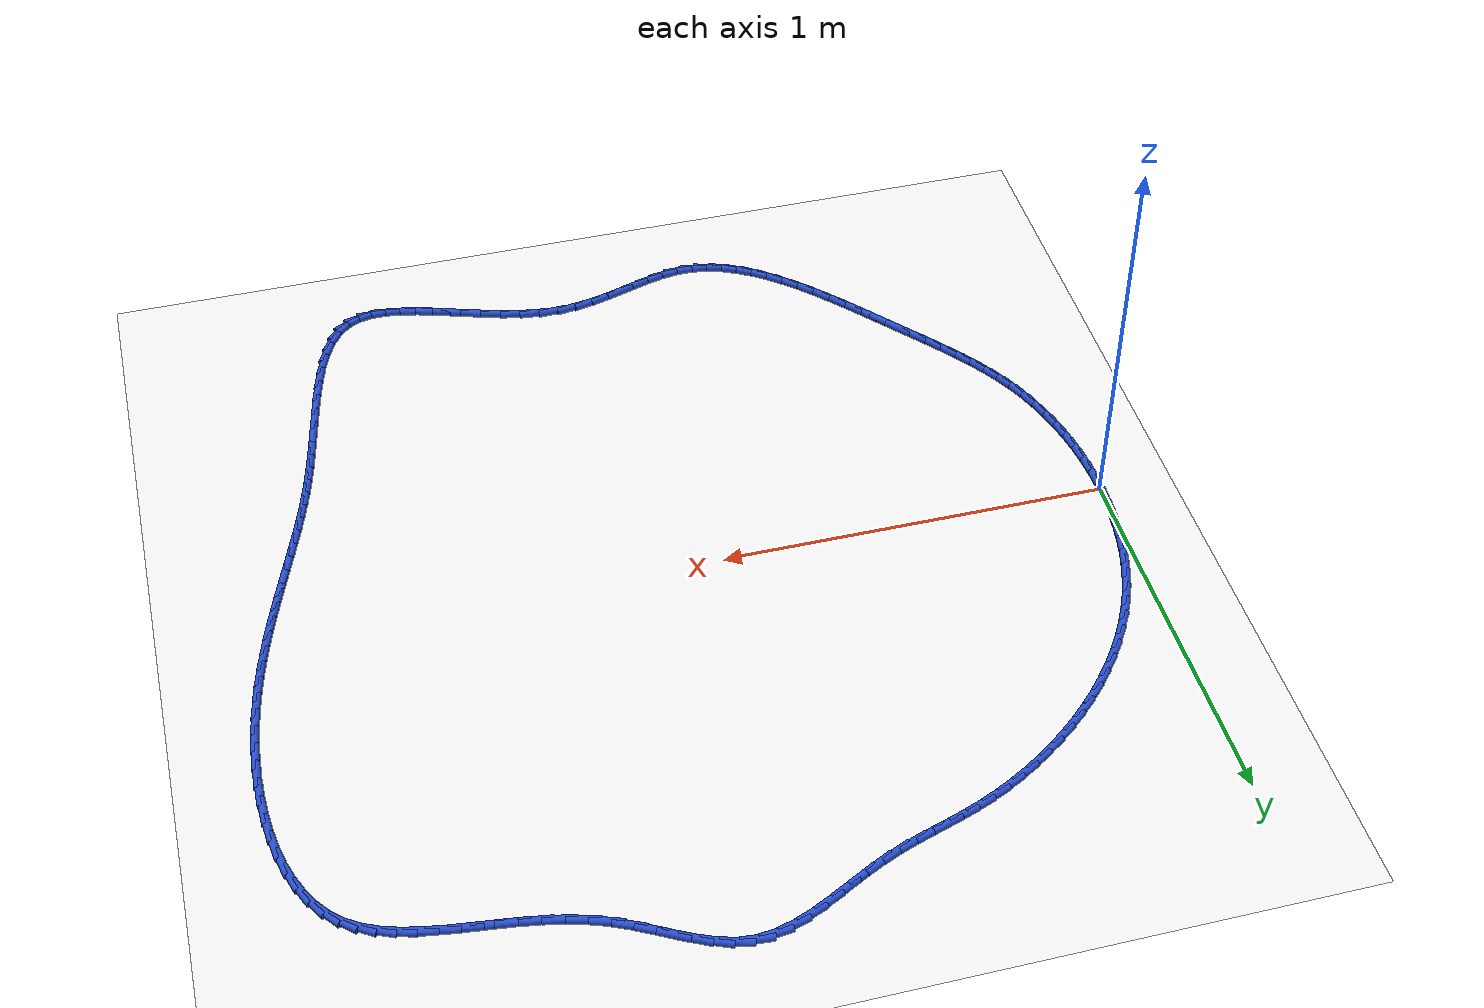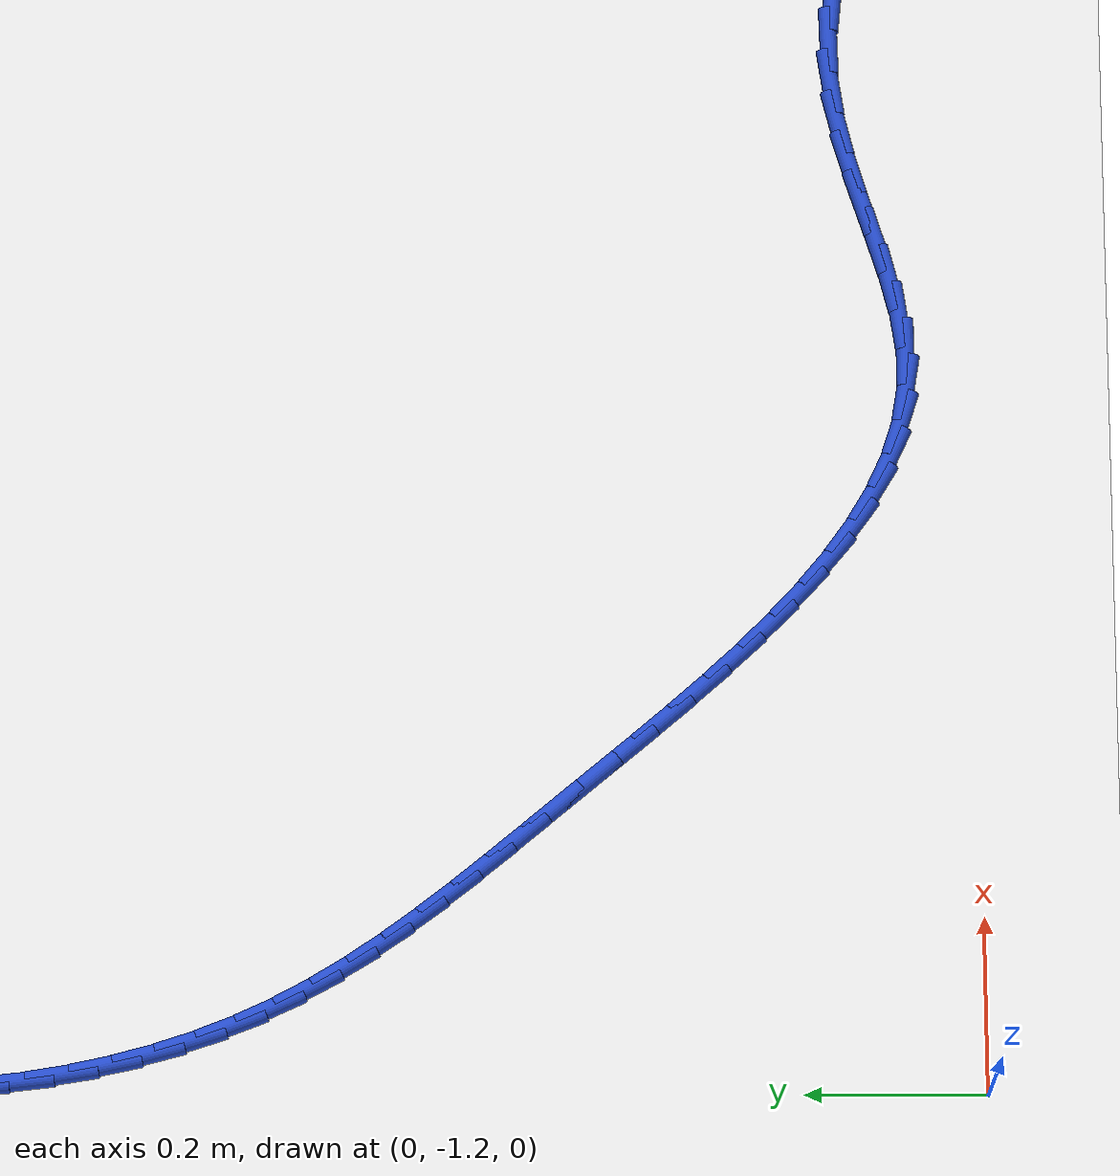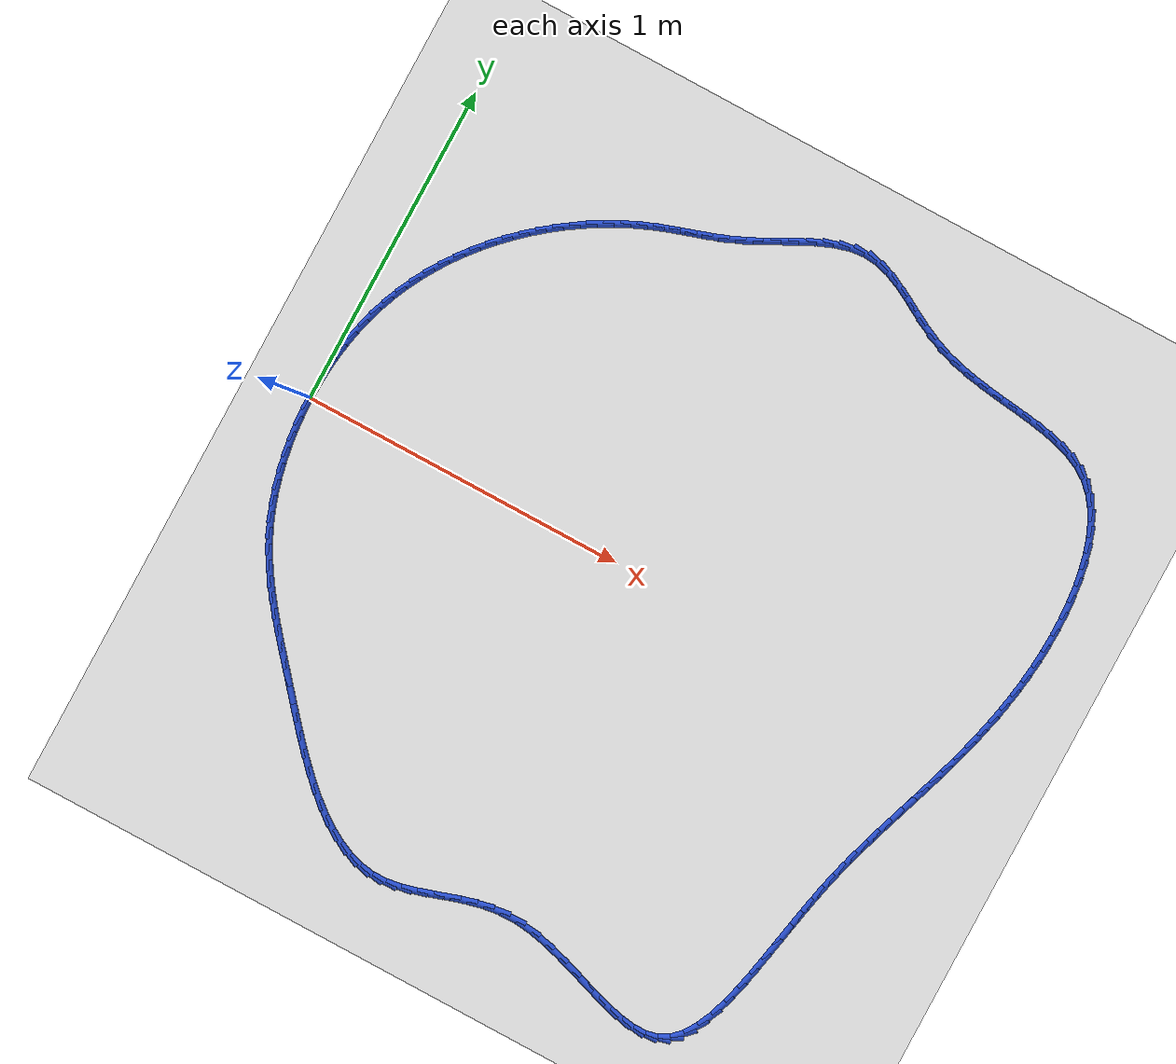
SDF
<sdf version="1.6">
 <world name="default">
  <light name="sun" type="directional">
   <pose>0 0 10 0 -0 0</pose>
   <diffuse>0.8 0.8 0.8 1</diffuse>
   <specular>0.2 0.2 0.2 1</specular>
   <attenuation>
    <range>1000</range>
    <constant>0.9</constant>
    <linear>0.01</linear>
    <quadratic>0.001</quadratic>
   </attenuation>
   <direction>-0.5 0.1 -0.9</direction>
  </light>
  <model name="ground_plane">
   <static>1</static>
   <link name="link">
    <collision name="collision">
     <geometry><plane><normal>0 0 1</normal><size>100 100</size></plane></geometry>
     <surface><friction><ode><mu>100</mu><mu2>50</mu2></ode></friction></surface>
    </collision>
    <visual name="visual">
     <cast_shadows>0</cast_shadows>
     <geometry><plane><normal>0 0 1</normal><size>100 100</size></plane></geometry>
     <material>
      <script><uri>file://media/materials/scripts/gazebo.material</uri><name>Gazebo/WhiteGlow</name></script>
     </material>
    </visual>
   </link>
  </model>
  <gravity>0 0 -9.8</gravity>
  <magnetic_field>6e-06 2.3e-05 -4.2e-05</magnetic_field>
  <atmosphere type="adiabatic"/>
  <physics name="default_physics" default="0" type="ode">
   <max_step_size>0.001</max_step_size>
   <real_time_factor>1</real_time_factor>
   <real_time_update_rate>1000</real_time_update_rate>
  </physics>
  <scene><ambient>0.4 0.4 0.4 1</ambient><background>0.7 0.7 0.7 1</background><shadows>1</shadows></scene>
  <spherical_coordinates>
   <surface_model>EARTH_WGS84</surface_model>
   <latitude_deg>0</latitude_deg>
   <longitude_deg>0</longitude_deg>
   <elevation>0</elevation>
   <heading_deg>0</heading_deg>
  </spherical_coordinates>
  <model name="line">
   <link name="link_0">
    <pose>2.6020852139652106e-17 4.163336342344337e-17 0.01 0 1.57 1.5517092501515306</pose>
    <collision name="collision">
     <geometry><cylinder><radius>0.01</radius><length>0.08</length></cylinder></geometry>
    </collision>
    <visual name="visual">
     <material>
      <script><name>Gazebo/Blue</name><uri>file://media/materials/scripts/gazebo.material</uri></script>
     </material>
     <geometry><cylinder><radius>0.01</radius><length>0.08</length></cylinder></geometry>
    </visual>
   </link>
   <link name="link_1">
    <pose>0.0009282315727998414 0.04862551055071367 0.01 0 1.57 1.5059344220400541</pose>
    <collision name="collision">
     <geometry><cylinder><radius>0.01</radius><length>0.08</length></cylinder></geometry>
    </collision>
    <visual name="visual">
     <material>
      <script><name>Gazebo/Blue</name><uri>file://media/materials/scripts/gazebo.material</uri></script>
     </material>
     <geometry><cylinder><radius>0.01</radius><length>0.08</length></cylinder></geometry>
    </visual>
   </link>
   <link name="link_2">
    <pose>0.004068738450870917 0.09697594902325075 0.01 0 1.57 1.4585347785168035</pose>
    <collision name="collision">
     <geometry><cylinder><radius>0.01</radius><length>0.08</length></cylinder></geometry>
    </collision>
    <visual name="visual">
     <material>
      <script><name>Gazebo/Blue</name><uri>file://media/materials/scripts/gazebo.material</uri></script>
     </material>
     <geometry><cylinder><radius>0.01</radius><length>0.08</length></cylinder></geometry>
    </visual>
   </link>
   <link name="link_3">
    <pose>0.009477584529107106 0.14495413128332335 0.01 0 1.57 1.4094362277293557</pose>
    <collision name="collision">
     <geometry><cylinder><radius>0.01</radius><length>0.08</length></cylinder></geometry>
    </collision>
    <visual name="visual">
     <material>
      <script><name>Gazebo/Blue</name><uri>file://media/materials/scripts/gazebo.material</uri></script>
     </material>
     <geometry><cylinder><radius>0.01</radius><length>0.08</length></cylinder></geometry>
    </visual>
   </link>
   <link name="link_4">
    <pose>0.017210833702402256 0.19246287319664337 0.01 0 1.57 1.3585893362925034</pose>
    <collision name="collision">
     <geometry><cylinder><radius>0.01</radius><length>0.08</length></cylinder></geometry>
    </collision>
    <visual name="visual">
     <material>
      <script><name>Gazebo/Blue</name><uri>file://media/materials/scripts/gazebo.material</uri></script>
     </material>
     <geometry><cylinder><radius>0.01</radius><length>0.08</length></cylinder></geometry>
    </visual>
   </link>
   <link name="link_5">
    <pose>0.027324549865650204 0.23940499062892273 0.01 0 1.57 1.305975027637463</pose>
    <collision name="collision">
     <geometry><cylinder><radius>0.01</radius><length>0.08</length></cylinder></geometry>
    </collision>
    <visual name="visual">
     <material>
      <script><name>Gazebo/Blue</name><uri>file://media/materials/scripts/gazebo.material</uri></script>
     </material>
     <geometry><cylinder><radius>0.01</radius><length>0.08</length></cylinder></geometry>
    </visual>
   </link>
   <link name="link_6">
    <pose>0.03987479691374483 0.28568329944587356 0.01 0 1.57 1.2516104366016096</pose>
    <collision name="collision">
     <geometry><cylinder><radius>0.01</radius><length>0.08</length></cylinder></geometry>
    </collision>
    <visual name="visual">
     <material>
      <script><name>Gazebo/Blue</name><uri>file://media/materials/scripts/gazebo.material</uri></script>
     </material>
     <geometry><cylinder><radius>0.01</radius><length>0.08</length></cylinder></geometry>
    </visual>
   </link>
   <link name="link_7">
    <pose>0.05491763874157994 0.3312006155132076 0.01 0 1.57 1.1955544581289477</pose>
    <collision name="collision">
     <geometry><cylinder><radius>0.01</radius><length>0.08</length></cylinder></geometry>
    </collision>
    <visual name="visual">
     <material>
      <script><name>Gazebo/Blue</name><uri>file://media/materials/scripts/gazebo.material</uri></script>
     </material>
     <geometry><cylinder><radius>0.01</radius><length>0.08</length></cylinder></geometry>
    </visual>
   </link>
   <link name="link_8">
    <pose>0.07250913924404942 0.375859754696637 0.01 0 1.57 1.13792915806571</pose>
    <collision name="collision">
     <geometry><cylinder><radius>0.01</radius><length>0.08</length></cylinder></geometry>
    </collision>
    <visual name="visual">
     <material>
      <script><name>Gazebo/Blue</name><uri>file://media/materials/scripts/gazebo.material</uri></script>
     </material>
     <geometry><cylinder><radius>0.01</radius><length>0.08</length></cylinder></geometry>
    </visual>
   </link>
   <link name="link_9">
    <pose>0.09270449270493479 0.4195635755722724 0.01 0 1.57 1.0801890849223204</pose>
    <collision name="collision">
     <geometry><cylinder><radius>0.01</radius><length>0.08</length></cylinder></geometry>
    </collision>
    <visual name="visual">
     <material>
      <script><name>Gazebo/Blue</name><uri>file://media/materials/scripts/gazebo.material</uri></script>
     </material>
     <geometry><cylinder><radius>0.01</radius><length>0.08</length></cylinder></geometry>
    </visual>
   </link>
   <link name="link_10">
    <pose>0.11548932728163748 0.4622183534124408 0.01 0 1.57 1.0245530205643905</pose>
    <collision name="collision">
     <geometry><cylinder><radius>0.01</radius><length>0.08</length></cylinder></geometry>
    </collision>
    <visual name="visual">
     <material>
      <script><name>Gazebo/Blue</name><uri>file://media/materials/scripts/gazebo.material</uri></script>
     </material>
     <geometry><cylinder><radius>0.01</radius><length>0.08</length></cylinder></geometry>
    </visual>
   </link>
   <link name="link_11">
    <pose>0.14073004081762283 0.5037362194107877 0.01 0 1.57 0.9710516705400668</pose>
    <collision name="collision">
     <geometry><cylinder><radius>0.01</radius><length>0.08</length></cylinder></geometry>
    </collision>
    <visual name="visual">
     <material>
      <script><name>Gazebo/Blue</name><uri>file://media/materials/scripts/gazebo.material</uri></script>
     </material>
     <geometry><cylinder><radius>0.01</radius><length>0.08</length></cylinder></geometry>
    </visual>
   </link>
   <link name="link_12">
    <pose>0.16828131561240942 0.5440298801624759 0.01 0 1.57 0.9194628288646522</pose>
    <collision name="collision">
     <geometry><cylinder><radius>0.01</radius><length>0.08</length></cylinder></geometry>
    </collision>
    <visual name="visual">
     <material>
      <script><name>Gazebo/Blue</name><uri>file://media/materials/scripts/gazebo.material</uri></script>
     </material>
     <geometry><cylinder><radius>0.01</radius><length>0.08</length></cylinder></geometry>
    </visual>
   </link>
   <link name="link_13">
    <pose>0.1979978339655158 0.5830120422626682 0.01 0 1.57 0.8695460932217859</pose>
    <collision name="collision">
     <geometry><cylinder><radius>0.01</radius><length>0.08</length></cylinder></geometry>
    </collision>
    <visual name="visual">
     <material>
      <script><name>Gazebo/Blue</name><uri>file://media/materials/scripts/gazebo.material</uri></script>
     </material>
     <geometry><cylinder><radius>0.01</radius><length>0.08</length></cylinder></geometry>
    </visual>
   </link>
   <link name="link_14">
    <pose>0.22973427817646047 0.6205954123065273 0.01 0 1.57 0.8210492619521321</pose>
    <collision name="collision">
     <geometry><cylinder><radius>0.01</radius><length>0.08</length></cylinder></geometry>
    </collision>
    <visual name="visual">
     <material>
      <script><name>Gazebo/Blue</name><uri>file://media/materials/scripts/gazebo.material</uri></script>
     </material>
     <geometry><cylinder><radius>0.01</radius><length>0.08</length></cylinder></geometry>
    </visual>
   </link>
   <link name="link_15">
    <pose>0.26334533054476206 0.6566926968892163 0.01 0 1.57 0.7737126452198714</pose>
    <collision name="collision">
     <geometry><cylinder><radius>0.01</radius><length>0.08</length></cylinder></geometry>
    </collision>
    <visual name="visual">
     <material>
      <script><name>Gazebo/Blue</name><uri>file://media/materials/scripts/gazebo.material</uri></script>
     </material>
     <geometry><cylinder><radius>0.01</radius><length>0.08</length></cylinder></geometry>
    </visual>
   </link>
   <link name="link_16">
    <pose>0.298685673369939 0.6912166026058972 0.01 0 1.57 0.7272716430369592</pose>
    <collision name="collision">
     <geometry><cylinder><radius>0.01</radius><length>0.08</length></cylinder></geometry>
    </collision>
    <visual name="visual">
     <material>
      <script><name>Gazebo/Blue</name><uri>file://media/materials/scripts/gazebo.material</uri></script>
     </material>
     <geometry><cylinder><radius>0.01</radius><length>0.08</length></cylinder></geometry>
    </visual>
   </link>
   <link name="link_17">
    <pose>0.33560998895150984 0.7240798360517334 0.01 0 1.57 0.6814579389573997</pose>
    <collision name="collision">
     <geometry><cylinder><radius>0.01</radius><length>0.08</length></cylinder></geometry>
    </collision>
    <visual name="visual">
     <material>
      <script><name>Gazebo/Blue</name><uri>file://media/materials/scripts/gazebo.material</uri></script>
     </material>
     <geometry><cylinder><radius>0.01</radius><length>0.08</length></cylinder></geometry>
    </visual>
   </link>
   <link name="link_18">
    <pose>0.37397295958899335 0.7551951038218877 0.01 0 1.57 0.6359996274307417</pose>
    <collision name="collision">
     <geometry><cylinder><radius>0.01</radius><length>0.08</length></cylinder></geometry>
    </collision>
    <visual name="visual">
     <material>
      <script><name>Gazebo/Blue</name><uri>file://media/materials/scripts/gazebo.material</uri></script>
     </material>
     <geometry><cylinder><radius>0.01</radius><length>0.08</length></cylinder></geometry>
    </visual>
   </link>
   <link name="link_19">
    <pose>0.41362926758190793 0.7844751125115226 0.01 0 1.57 0.5906205551514397</pose>
    <collision name="collision">
     <geometry><cylinder><radius>0.01</radius><length>0.08</length></cylinder></geometry>
    </collision>
    <visual name="visual">
     <material>
      <script><name>Gazebo/Blue</name><uri>file://media/materials/scripts/gazebo.material</uri></script>
     </material>
     <geometry><cylinder><radius>0.01</radius><length>0.08</length></cylinder></geometry>
    </visual>
   </link>
   <link name="link_20">
    <pose>0.45443359522977195 0.8118325687158011 0.01 0 1.57 0.5450391253985567</pose>
    <collision name="collision">
     <geometry><cylinder><radius>0.01</radius><length>0.08</length></cylinder></geometry>
    </collision>
    <visual name="visual">
     <material>
      <script><name>Gazebo/Blue</name><uri>file://media/materials/scripts/gazebo.material</uri></script>
     </material>
     <geometry><cylinder><radius>0.01</radius><length>0.08</length></cylinder></geometry>
    </visual>
   </link>
   <link name="link_21">
    <pose>0.49624062483210446 0.837180179029886 0.01 0 1.57 0.49896679790513515</pose>
    <collision name="collision">
     <geometry><cylinder><radius>0.01</radius><length>0.08</length></cylinder></geometry>
    </collision>
    <visual name="visual">
     <material>
      <script><name>Gazebo/Blue</name><uri>file://media/materials/scripts/gazebo.material</uri></script>
     </material>
     <geometry><cylinder><radius>0.01</radius><length>0.08</length></cylinder></geometry>
    </visual>
   </link>
   <link name="link_22">
    <pose>0.5389050386884234 0.8604306500489398 0.01 0 1.57 0.4521065213377699</pose>
    <collision name="collision">
     <geometry><cylinder><radius>0.01</radius><length>0.08</length></cylinder></geometry>
    </collision>
    <visual name="visual">
     <material>
      <script><name>Gazebo/Blue</name><uri>file://media/materials/scripts/gazebo.material</uri></script>
     </material>
     <geometry><cylinder><radius>0.01</radius><length>0.08</length></cylinder></geometry>
    </visual>
   </link>
   <link name="link_23">
    <pose>0.5822815190982479 0.8814966883681254 0.01 0 1.57 0.4041513661111556</pose>
    <collision name="collision">
     <geometry><cylinder><radius>0.01</radius><length>0.08</length></cylinder></geometry>
    </collision>
    <visual name="visual">
     <material>
      <script><name>Gazebo/Blue</name><uri>file://media/materials/scripts/gazebo.material</uri></script>
     </material>
     <geometry><cylinder><radius>0.01</radius><length>0.08</length></cylinder></geometry>
    </visual>
   </link>
   <link name="link_24">
    <pose>0.6262247483610961 0.9002910005826059 0.01 0 1.57 0.35673341838341655</pose>
    <collision name="collision">
     <geometry><cylinder><radius>0.01</radius><length>0.08</length></cylinder></geometry>
    </collision>
    <visual name="visual">
     <material>
      <script><name>Gazebo/Blue</name><uri>file://media/materials/scripts/gazebo.material</uri></script>
     </material>
     <geometry><cylinder><radius>0.01</radius><length>0.08</length></cylinder></geometry>
    </visual>
   </link>
   <link name="link_25">
    <pose>0.6705960522285797 0.9168272107083539 0.01 0 1.57 0.32435083888574384</pose>
    <collision name="collision">
     <geometry><cylinder><radius>0.01</radius><length>0.08</length></cylinder></geometry>
    </collision>
    <visual name="visual">
     <material>
      <script><name>Gazebo/Blue</name><uri>file://media/materials/scripts/gazebo.material</uri></script>
     </material>
     <geometry><cylinder><radius>0.01</radius><length>0.08</length></cylinder></geometry>
    </visual>
   </link>
   <link name="link_26">
    <pose>0.7153055178400789 0.931859653075764 0.01 0 1.57 0.3141249661949306</pose>
    <collision name="collision">
     <geometry><cylinder><radius>0.01</radius><length>0.08</length></cylinder></geometry>
    </collision>
    <visual name="visual">
     <material>
      <script><name>Gazebo/Blue</name><uri>file://media/materials/scripts/gazebo.material</uri></script>
     </material>
     <geometry><cylinder><radius>0.01</radius><length>0.08</length></cylinder></geometry>
    </visual>
   </link>
   <link name="link_27">
    <pose>0.7602849558181854 0.9464726527890197 0.01 0 1.57 0.3261057442350908</pose>
    <collision name="collision">
     <geometry><cylinder><radius>0.01</radius><length>0.08</length></cylinder></geometry>
    </collision>
    <visual name="visual">
     <material>
      <script><name>Gazebo/Blue</name><uri>file://media/materials/scripts/gazebo.material</uri></script>
     </material>
     <geometry><cylinder><radius>0.01</radius><length>0.08</length></cylinder></geometry>
    </visual>
   </link>
   <link name="link_28">
    <pose>0.8054662764676969 0.9617520491757628 0.01 0 1.57 0.35951464128054117</pose>
    <collision name="collision">
     <geometry><cylinder><radius>0.01</radius><length>0.08</length></cylinder></geometry>
    </collision>
    <visual name="visual">
     <material>
      <script><name>Gazebo/Blue</name><uri>file://media/materials/scripts/gazebo.material</uri></script>
     </material>
     <geometry><cylinder><radius>0.01</radius><length>0.08</length></cylinder></geometry>
    </visual>
   </link>
   <link name="link_29">
    <pose>0.8507813900934104 0.9787836815636339 0.01 0 1.57 0.41233403289446163</pose>
    <collision name="collision">
     <geometry><cylinder><radius>0.01</radius><length>0.08</length></cylinder></geometry>
    </collision>
    <visual name="visual">
     <material>
      <script><name>Gazebo/Blue</name><uri>file://media/materials/scripts/gazebo.material</uri></script>
     </material>
     <geometry><cylinder><radius>0.01</radius><length>0.08</length></cylinder></geometry>
    </visual>
   </link>
   <link name="link_30">
    <pose>0.896162079093217 0.9986336019622885 0.01 0 1.57 0.46344411020995363</pose>
    <collision name="collision">
     <geometry><cylinder><radius>0.01</radius><length>0.08</length></cylinder></geometry>
    </collision>
    <visual name="visual">
     <material>
      <script><name>Gazebo/Blue</name><uri>file://media/materials/scripts/gazebo.material</uri></script>
     </material>
     <geometry><cylinder><radius>0.01</radius><length>0.08</length></cylinder></geometry>
    </visual>
   </link>
   <link name="link_31">
    <pose>0.9415332726181174 1.0213076586699956 0.01 0 1.57 0.4862088964064303</pose>
    <collision name="collision">
     <geometry><cylinder><radius>0.01</radius><length>0.08</length></cylinder></geometry>
    </collision>
    <visual name="visual">
     <material>
      <script><name>Gazebo/Blue</name><uri>file://media/materials/scripts/gazebo.material</uri></script>
     </material>
     <geometry><cylinder><radius>0.01</radius><length>0.08</length></cylinder></geometry>
    </visual>
   </link>
   <link name="link_32">
    <pose>0.9868097243360935 1.0452375432344176 0.01 0 1.57 0.48021782444834926</pose>
    <collision name="collision">
     <geometry><cylinder><radius>0.01</radius><length>0.08</length></cylinder></geometry>
    </collision>
    <visual name="visual">
     <material>
      <script><name>Gazebo/Blue</name><uri>file://media/materials/scripts/gazebo.material</uri></script>
     </material>
     <geometry><cylinder><radius>0.01</radius><length>0.08</length></cylinder></geometry>
    </visual>
   </link>
   <link name="link_33">
    <pose>1.031905362846944 1.0687273083826176 0.01 0 1.57 0.44454053958479745</pose>
    <collision name="collision">
     <geometry><cylinder><radius>0.01</radius><length>0.08</length></cylinder></geometry>
    </collision>
    <visual name="visual">
     <material>
      <script><name>Gazebo/Blue</name><uri>file://media/materials/scripts/gazebo.material</uri></script>
     </material>
     <geometry><cylinder><radius>0.01</radius><length>0.08</length></cylinder></geometry>
    </visual>
   </link>
   <link name="link_34">
    <pose>1.0767341167504672 1.0900810068416598 0.01 0 1.57 0.37528864417723795</pose>
    <collision name="collision">
     <geometry><cylinder><radius>0.01</radius><length>0.08</length></cylinder></geometry>
    </collision>
    <visual name="visual">
     <material>
      <script><name>Gazebo/Blue</name><uri>file://media/materials/scripts/gazebo.material</uri></script>
     </material>
     <geometry><cylinder><radius>0.01</radius><length>0.08</length></cylinder></geometry>
    </visual>
   </link>
   <link name="link_35">
    <pose>1.1212099146464627 1.1076026913386081 0.01 0 1.57 0.2659073901883522</pose>
    <collision name="collision">
     <geometry><cylinder><radius>0.01</radius><length>0.08</length></cylinder></geometry>
    </collision>
    <visual name="visual">
     <material>
      <script><name>Gazebo/Blue</name><uri>file://media/materials/scripts/gazebo.material</uri></script>
     </material>
     <geometry><cylinder><radius>0.01</radius><length>0.08</length></cylinder></geometry>
    </visual>
   </link>
   <link name="link_36">
    <pose>1.1652466851347287 1.1195964146005262 0.01 0 1.57 0.10918553733953469</pose>
    <collision name="collision">
     <geometry><cylinder><radius>0.01</radius><length>0.08</length></cylinder></geometry>
    </collision>
    <visual name="visual">
     <material>
      <script><name>Gazebo/Blue</name><uri>file://media/materials/scripts/gazebo.material</uri></script>
     </material>
     <geometry><cylinder><radius>0.01</radius><length>0.08</length></cylinder></geometry>
    </visual>
   </link>
   <link name="link_37">
    <pose>1.208758356815064 1.1243662293544778 0.01 0 1.57 -0.09324090817124653</pose>
    <collision name="collision">
     <geometry><cylinder><radius>0.01</radius><length>0.08</length></cylinder></geometry>
    </collision>
    <visual name="visual">
     <material>
      <script><name>Gazebo/Blue</name><uri>file://media/materials/scripts/gazebo.material</uri></script>
     </material>
     <geometry><cylinder><radius>0.01</radius><length>0.08</length></cylinder></geometry>
    </visual>
   </link>
   <link name="link_38">
    <pose>1.251675765536862 1.1203529340907725 0.01 0 1.57 -0.28144342441612075</pose>
    <collision name="collision">
     <geometry><cylinder><radius>0.01</radius><length>0.08</length></cylinder></geometry>
    </collision>
    <visual name="visual">
     <material>
      <script><name>Gazebo/Blue</name><uri>file://media/materials/scripts/gazebo.material</uri></script>
     </material>
     <geometry><cylinder><radius>0.01</radius><length>0.08</length></cylinder></geometry>
    </visual>
   </link>
   <link name="link_39">
    <pose>1.2941851132195041 1.1080627269942185 0.01 0 1.57 -0.4099132603606312</pose>
    <collision name="collision">
     <geometry><cylinder><radius>0.01</radius><length>0.08</length></cylinder></geometry>
    </collision>
    <visual name="visual">
     <material>
      <script><name>Gazebo/Blue</name><uri>file://media/materials/scripts/gazebo.material</uri></script>
     </material>
     <geometry><cylinder><radius>0.01</radius><length>0.08</length></cylinder></geometry>
    </visual>
   </link>
   <link name="link_40">
    <pose>1.3366704093119068 1.089601672712271 0.01 0 1.57 -0.48322082847087755</pose>
    <collision name="collision">
     <geometry><cylinder><radius>0.01</radius><length>0.08</length></cylinder></geometry>
    </collision>
    <visual name="visual">
     <material>
      <script><name>Gazebo/Blue</name><uri>file://media/materials/scripts/gazebo.material</uri></script>
     </material>
     <geometry><cylinder><radius>0.01</radius><length>0.08</length></cylinder></geometry>
    </visual>
   </link>
   <link name="link_41">
    <pose>1.379520822895022 1.0671175669744668 0.01 0 1.57 -0.5094529541910356</pose>
    <collision name="collision">
     <geometry><cylinder><radius>0.01</radius><length>0.08</length></cylinder></geometry>
    </collision>
    <visual name="visual">
     <material>
      <script><name>Gazebo/Blue</name><uri>file://media/materials/scripts/gazebo.material</uri></script>
     </material>
     <geometry><cylinder><radius>0.01</radius><length>0.08</length></cylinder></geometry>
    </visual>
   </link>
   <link name="link_42">
    <pose>1.4231255230497994 1.042758205510342 0.01 0 1.57 -0.4937968843412767</pose>
    <collision name="collision">
     <geometry><cylinder><radius>0.01</radius><length>0.08</length></cylinder></geometry>
    </collision>
    <visual name="visual">
     <material>
      <script><name>Gazebo/Blue</name><uri>file://media/materials/scripts/gazebo.material</uri></script>
     </material>
     <geometry><cylinder><radius>0.01</radius><length>0.08</length></cylinder></geometry>
    </visual>
   </link>
   <link name="link_43">
    <pose>1.4678736788571909 1.0186713840494332 0.01 0 1.57 -0.4378469843174447</pose>
    <collision name="collision">
     <geometry><cylinder><radius>0.01</radius><length>0.08</length></cylinder></geometry>
    </collision>
    <visual name="visual">
     <material>
      <script><name>Gazebo/Blue</name><uri>file://media/materials/scripts/gazebo.material</uri></script>
     </material>
     <geometry><cylinder><radius>0.01</radius><length>0.08</length></cylinder></geometry>
    </visual>
   </link>
   <link name="link_44">
    <pose>1.5141544593981466 0.9970048983212765 0.01 0 1.57 -0.34772131931239236</pose>
    <collision name="collision">
     <geometry><cylinder><radius>0.01</radius><length>0.08</length></cylinder></geometry>
    </collision>
    <visual name="visual">
     <material>
      <script><name>Gazebo/Blue</name><uri>file://media/materials/scripts/gazebo.material</uri></script>
     </material>
     <geometry><cylinder><radius>0.01</radius><length>0.08</length></cylinder></geometry>
    </visual>
   </link>
   <link name="link_45">
    <pose>1.5622547275222343 0.9795710364104616 0.01 0 1.57 -0.2635306501707892</pose>
    <collision name="collision">
     <geometry><cylinder><radius>0.01</radius><length>0.08</length></cylinder></geometry>
    </collision>
    <visual name="visual">
     <material>
      <script><name>Gazebo/Blue</name><uri>file://media/materials/scripts/gazebo.material</uri></script>
     </material>
     <geometry><cylinder><radius>0.01</radius><length>0.08</length></cylinder></geometry>
    </visual>
   </link>
   <link name="link_46">
    <pose>1.6118535902458673 0.9661889846567295 0.01 0 1.57 -0.1999344946143437</pose>
    <collision name="collision">
     <geometry><cylinder><radius>0.01</radius><length>0.08</length></cylinder></geometry>
    </collision>
    <visual name="visual">
     <material>
      <script><name>Gazebo/Blue</name><uri>file://media/materials/scripts/gazebo.material</uri></script>
     </material>
     <geometry><cylinder><radius>0.01</radius><length>0.08</length></cylinder></geometry>
    </visual>
   </link>
   <link name="link_47">
    <pose>1.6624066101415789 0.9559448277217211 0.01 0 1.57 -0.15611593324082026</pose>
    <collision name="collision">
     <geometry><cylinder><radius>0.01</radius><length>0.08</length></cylinder></geometry>
    </collision>
    <visual name="visual">
     <material>
      <script><name>Gazebo/Blue</name><uri>file://media/materials/scripts/gazebo.material</uri></script>
     </material>
     <geometry><cylinder><radius>0.01</radius><length>0.08</length></cylinder></geometry>
    </visual>
   </link>
   <link name="link_48">
    <pose>1.7133690034115359 0.9479235143645645 0.01 0 1.57 -0.13132555788795894</pose>
    <collision name="collision">
     <geometry><cylinder><radius>0.01</radius><length>0.08</length></cylinder></geometry>
    </collision>
    <visual name="visual">
     <material>
      <script><name>Gazebo/Blue</name><uri>file://media/materials/scripts/gazebo.material</uri></script>
     </material>
     <geometry><cylinder><radius>0.01</radius><length>0.08</length></cylinder></geometry>
    </visual>
   </link>
   <link name="link_49">
    <pose>1.7641959862579037 0.9412099933443877 0.01 0 1.57 -0.12538433362558804</pose>
    <collision name="collision">
     <geometry><cylinder><radius>0.01</radius><length>0.08</length></cylinder></geometry>
    </collision>
    <visual name="visual">
     <material>
      <script><name>Gazebo/Blue</name><uri>file://media/materials/scripts/gazebo.material</uri></script>
     </material>
     <geometry><cylinder><radius>0.01</radius><length>0.08</length></cylinder></geometry>
    </visual>
   </link>
   <link name="link_50">
    <pose>1.8143427748828516 0.9348892134203192 0.01 0 1.57 -0.13897638585494634</pose>
    <collision name="collision">
     <geometry><cylinder><radius>0.01</radius><length>0.08</length></cylinder></geometry>
    </collision>
    <visual name="visual">
     <material>
      <script><name>Gazebo/Blue</name><uri>file://media/materials/scripts/gazebo.material</uri></script>
     </material>
     <geometry><cylinder><radius>0.01</radius><length>0.08</length></cylinder></geometry>
    </visual>
   </link>
   <link name="link_51">
    <pose>1.8632645854885446 0.9280461233514871 0.01 0 1.57 -0.1738391282583893</pose>
    <collision name="collision">
     <geometry><cylinder><radius>0.01</radius><length>0.08</length></cylinder></geometry>
    </collision>
    <visual name="visual">
     <material>
      <script><name>Gazebo/Blue</name><uri>file://media/materials/scripts/gazebo.material</uri></script>
     </material>
     <geometry><cylinder><radius>0.01</radius><length>0.08</length></cylinder></geometry>
    </visual>
   </link>
   <link name="link_52">
    <pose>1.9104166342771505 0.91976567189702 0.01 0 1.57 -0.23284107659925676</pose>
    <collision name="collision">
     <geometry><cylinder><radius>0.01</radius><length>0.08</length></cylinder></geometry>
    </collision>
    <visual name="visual">
     <material>
      <script><name>Gazebo/Blue</name><uri>file://media/materials/scripts/gazebo.material</uri></script>
     </material>
     <geometry><cylinder><radius>0.01</radius><length>0.08</length></cylinder></geometry>
    </visual>
   </link>
   <link name="link_53">
    <pose>1.9552541374508363 0.9091328078160458 0.01 0 1.57 -0.31976829064523693</pose>
    <collision name="collision">
     <geometry><cylinder><radius>0.01</radius><length>0.08</length></cylinder></geometry>
    </collision>
    <visual name="visual">
     <material>
      <script><name>Gazebo/Blue</name><uri>file://media/materials/scripts/gazebo.material</uri></script>
     </material>
     <geometry><cylinder><radius>0.01</radius><length>0.08</length></cylinder></geometry>
    </visual>
   </link>
   <link name="link_54">
    <pose>1.9972323112117696 0.8952324798676929 0.01 0 1.57 -0.4383631733152013</pose>
    <collision name="collision">
     <geometry><cylinder><radius>0.01</radius><length>0.08</length></cylinder></geometry>
    </collision>
    <visual name="visual">
     <material>
      <script><name>Gazebo/Blue</name><uri>file://media/materials/scripts/gazebo.material</uri></script>
     </material>
     <geometry><cylinder><radius>0.01</radius><length>0.08</length></cylinder></geometry>
    </visual>
   </link>
   <link name="link_55">
    <pose>2.0358063717621153 0.8771496368110895 0.01 0 1.57 -0.5899388915917941</pose>
    <collision name="collision">
     <geometry><cylinder><radius>0.01</radius><length>0.08</length></cylinder></geometry>
    </collision>
    <visual name="visual">
     <material>
      <script><name>Gazebo/Blue</name><uri>file://media/materials/scripts/gazebo.material</uri></script>
     </material>
     <geometry><cylinder><radius>0.01</radius><length>0.08</length></cylinder></geometry>
    </visual>
   </link>
   <link name="link_56">
    <pose>2.0704315353040426 0.853969227405364 0.01 0 1.57 -0.7642307128121009</pose>
    <collision name="collision">
     <geometry><cylinder><radius>0.01</radius><length>0.08</length></cylinder></geometry>
    </collision>
    <visual name="visual">
     <material>
      <script><name>Gazebo/Blue</name><uri>file://media/materials/scripts/gazebo.material</uri></script>
     </material>
     <geometry><cylinder><radius>0.01</radius><length>0.08</length></cylinder></geometry>
    </visual>
   </link>
   <link name="link_57">
    <pose>2.1006666066493054 0.8249878054975908 0.01 0 1.57 -0.9255778618217122</pose>
    <collision name="collision">
     <geometry><cylinder><radius>0.01</radius><length>0.08</length></cylinder></geometry>
    </collision>
    <visual name="visual">
     <material>
      <script><name>Gazebo/Blue</name><uri>file://media/materials/scripts/gazebo.material</uri></script>
     </material>
     <geometry><cylinder><radius>0.01</radius><length>0.08</length></cylinder></geometry>
    </visual>
   </link>
   <link name="link_58">
    <pose>2.126585049465974 0.7905532416093803 0.01 0 1.57 -1.0627380888356026</pose>
    <collision name="collision">
     <geometry><cylinder><radius>0.01</radius><length>0.08</length></cylinder></geometry>
    </collision>
    <visual name="visual">
     <material>
      <script><name>Gazebo/Blue</name><uri>file://media/materials/scripts/gazebo.material</uri></script>
     </material>
     <geometry><cylinder><radius>0.01</radius><length>0.08</length></cylinder></geometry>
    </visual>
   </link>
   <link name="link_59">
    <pose>2.1484198575501425 0.7513392855931439 0.01 0 1.57 -1.1772957390102776</pose>
    <collision name="collision">
     <geometry><cylinder><radius>0.01</radius><length>0.08</length></cylinder></geometry>
    </collision>
    <visual name="visual">
     <material>
      <script><name>Gazebo/Blue</name><uri>file://media/materials/scripts/gazebo.material</uri></script>
     </material>
     <geometry><cylinder><radius>0.01</radius><length>0.08</length></cylinder></geometry>
    </visual>
   </link>
   <link name="link_60">
    <pose>2.166404073175682 0.708019786329008 0.01 0 1.57 -1.2726553511147958</pose>
    <collision name="collision">
     <geometry><cylinder><radius>0.01</radius><length>0.08</length></cylinder></geometry>
    </collision>
    <visual name="visual">
     <material>
      <script><name>Gazebo/Blue</name><uri>file://media/materials/scripts/gazebo.material</uri></script>
     </material>
     <geometry><cylinder><radius>0.01</radius><length>0.08</length></cylinder></geometry>
    </visual>
   </link>
   <link name="link_61">
    <pose>2.180770738616458 0.6612685926970983 0.01 0 1.57 -1.3525095050085383</pose>
    <collision name="collision">
     <geometry><cylinder><radius>0.01</radius><length>0.08</length></cylinder></geometry>
    </collision>
    <visual name="visual">
     <material>
      <script><name>Gazebo/Blue</name><uri>file://media/materials/scripts/gazebo.material</uri></script>
     </material>
     <geometry><cylinder><radius>0.01</radius><length>0.08</length></cylinder></geometry>
    </visual>
   </link>
   <link name="link_62">
    <pose>2.1917528961463426 0.611759553577541 0.01 0 1.57 -1.4201678810788538</pose>
    <collision name="collision">
     <geometry><cylinder><radius>0.01</radius><length>0.08</length></cylinder></geometry>
    </collision>
    <visual name="visual">
     <material>
      <script><name>Gazebo/Blue</name><uri>file://media/materials/scripts/gazebo.material</uri></script>
     </material>
     <geometry><cylinder><radius>0.01</radius><length>0.08</length></cylinder></geometry>
    </visual>
   </link>
   <link name="link_63">
    <pose>2.199583588039202 0.560166517850463 0.01 0 1.57 -1.478381572556269</pose>
    <collision name="collision">
     <geometry><cylinder><radius>0.01</radius><length>0.08</length></cylinder></geometry>
    </collision>
    <visual name="visual">
     <material>
      <script><name>Gazebo/Blue</name><uri>file://media/materials/scripts/gazebo.material</uri></script>
     </material>
     <geometry><cylinder><radius>0.01</radius><length>0.08</length></cylinder></geometry>
    </visual>
   </link>
   <link name="link_64">
    <pose>2.204495856568906 0.5071633343959906 0.01 0 1.57 -1.5293814485798447</pose>
    <collision name="collision">
     <geometry><cylinder><radius>0.01</radius><length>0.08</length></cylinder></geometry>
    </collision>
    <visual name="visual">
     <material>
      <script><name>Gazebo/Blue</name><uri>file://media/materials/scripts/gazebo.material</uri></script>
     </material>
     <geometry><cylinder><radius>0.01</radius><length>0.08</length></cylinder></geometry>
    </visual>
   </link>
   <link name="link_65">
    <pose>2.2067227440093227 0.45342385209424996 0.01 0 1.57 1.5666059558191854</pose>
    <collision name="collision">
     <geometry><cylinder><radius>0.01</radius><length>0.08</length></cylinder></geometry>
    </collision>
    <visual name="visual">
     <material>
      <script><name>Gazebo/Blue</name><uri>file://media/materials/scripts/gazebo.material</uri></script>
     </material>
     <geometry><cylinder><radius>0.01</radius><length>0.08</length></cylinder></geometry>
    </visual>
   </link>
   <link name="link_66">
    <pose>2.206497292634322 0.3996219198253673 0.01 0 1.57 1.5248662973916567</pose>
    <collision name="collision">
     <geometry><cylinder><radius>0.01</radius><length>0.08</length></cylinder></geometry>
    </collision>
    <visual name="visual">
     <material>
      <script><name>Gazebo/Blue</name><uri>file://media/materials/scripts/gazebo.material</uri></script>
     </material>
     <geometry><cylinder><radius>0.01</radius><length>0.08</length></cylinder></geometry>
    </visual>
   </link>
   <link name="link_67">
    <pose>2.2040525129534476 0.346431004685043 0.01 0 1.57 1.485643464621398</pose>
    <collision name="collision">
     <geometry><cylinder><radius>0.01</radius><length>0.08</length></cylinder></geometry>
    </collision>
    <visual name="visual">
     <material>
      <script><name>Gazebo/Blue</name><uri>file://media/materials/scripts/gazebo.material</uri></script>
     </material>
     <geometry><cylinder><radius>0.01</radius><length>0.08</length></cylinder></geometry>
    </visual>
   </link>
   <link name="link_68">
    <pose>2.199605923424909 0.29433837039423727 0.01 0 1.57 1.4484267713915997</pose>
    <collision name="collision">
     <geometry><cylinder><radius>0.01</radius><length>0.08</length></cylinder></geometry>
    </collision>
    <visual name="visual">
     <material>
      <script><name>Gazebo/Blue</name><uri>file://media/materials/scripts/gazebo.material</uri></script>
     </material>
     <geometry><cylinder><radius>0.01</radius><length>0.08</length></cylinder></geometry>
    </visual>
   </link>
   <link name="link_69">
    <pose>2.1933346494123604 0.24334578457300018 0.01 0 1.57 1.413501222588842</pose>
    <collision name="collision">
     <geometry><cylinder><radius>0.01</radius><length>0.08</length></cylinder></geometry>
    </collision>
    <visual name="visual">
     <material>
      <script><name>Gazebo/Blue</name><uri>file://media/materials/scripts/gazebo.material</uri></script>
     </material>
     <geometry><cylinder><radius>0.01</radius><length>0.08</length></cylinder></geometry>
    </visual>
   </link>
   <link name="link_70">
    <pose>2.1854093159407784 0.19337688542049475 0.01 0 1.57 1.3811711624557867</pose>
    <collision name="collision">
     <geometry><cylinder><radius>0.01</radius><length>0.08</length></cylinder></geometry>
    </collision>
    <visual name="visual">
     <material>
      <script><name>Gazebo/Blue</name><uri>file://media/materials/scripts/gazebo.material</uri></script>
     </material>
     <geometry><cylinder><radius>0.01</radius><length>0.08</length></cylinder></geometry>
    </visual>
   </link>
   <link name="link_71">
    <pose>2.176000548035135 0.14435531113588299 0.01 0 1.57 1.3517030758279434</pose>
    <collision name="collision">
     <geometry><cylinder><radius>0.01</radius><length>0.08</length></cylinder></geometry>
    </collision>
    <visual name="visual">
     <material>
      <script><name>Gazebo/Blue</name><uri>file://media/materials/scripts/gazebo.material</uri></script>
     </material>
     <geometry><cylinder><radius>0.01</radius><length>0.08</length></cylinder></geometry>
    </visual>
   </link>
   <link name="link_72">
    <pose>2.1652789707204074 0.0962046999183285 0.01 0 1.57 1.325325647583155</pose>
    <collision name="collision">
     <geometry><cylinder><radius>0.01</radius><length>0.08</length></cylinder></geometry>
    </collision>
    <visual name="visual">
     <material>
      <script><name>Gazebo/Blue</name><uri>file://media/materials/scripts/gazebo.material</uri></script>
     </material>
     <geometry><cylinder><radius>0.01</radius><length>0.08</length></cylinder></geometry>
    </visual>
   </link>
   <link name="link_73">
    <pose>2.1534152090215684 0.0488486899669935 0.01 0 1.57 1.3022320957081772</pose>
    <collision name="collision">
     <geometry><cylinder><radius>0.01</radius><length>0.08</length></cylinder></geometry>
    </collision>
    <visual name="visual">
     <material>
      <script><name>Gazebo/Blue</name><uri>file://media/materials/scripts/gazebo.material</uri></script>
     </material>
     <geometry><cylinder><radius>0.01</radius><length>0.08</length></cylinder></geometry>
    </visual>
   </link>
   <link name="link_74">
    <pose>2.140579887963593 0.00221091948104081 0.01 0 1.57 1.2825841393424466</pose>
    <collision name="collision">
     <geometry><cylinder><radius>0.01</radius><length>0.08</length></cylinder></geometry>
    </collision>
    <visual name="visual">
     <material>
      <script><name>Gazebo/Blue</name><uri>file://media/materials/scripts/gazebo.material</uri></script>
     </material>
     <geometry><cylinder><radius>0.01</radius><length>0.08</length></cylinder></geometry>
    </visual>
   </link>
   <link name="link_75">
    <pose>2.1269436325714555 -0.04378497334036703 0.01 0 1.57 1.2665169164288894</pose>
    <collision name="collision">
     <geometry><cylinder><radius>0.01</radius><length>0.08</length></cylinder></geometry>
    </collision>
    <visual name="visual">
     <material>
      <script><name>Gazebo/Blue</name><uri>file://media/materials/scripts/gazebo.material</uri></script>
     </material>
     <geometry><cylinder><radius>0.01</radius><length>0.08</length></cylinder></geometry>
    </visual>
   </link>
   <link name="link_76">
    <pose>2.1126770678701305 -0.08921535029806768 0.01 0 1.57 1.2541441993549196</pose>
    <collision name="collision">
     <geometry><cylinder><radius>0.01</radius><length>0.08</length></cylinder></geometry>
    </collision>
    <visual name="visual">
     <material>
      <script><name>Gazebo/Blue</name><uri>file://media/materials/scripts/gazebo.material</uri></script>
     </material>
     <geometry><cylinder><radius>0.01</radius><length>0.08</length></cylinder></geometry>
    </visual>
   </link>
   <link name="link_77">
    <pose>2.0979508188845926 -0.13415657319289803 0.01 0 1.57 1.2455633368691363</pose>
    <collision name="collision">
     <geometry><cylinder><radius>0.01</radius><length>0.08</length></cylinder></geometry>
    </collision>
    <visual name="visual">
     <material>
      <script><name>Gazebo/Blue</name><uri>file://media/materials/scripts/gazebo.material</uri></script>
     </material>
     <geometry><cylinder><radius>0.01</radius><length>0.08</length></cylinder></geometry>
    </visual>
   </link>
   <link name="link_78">
    <pose>2.0829355106398157 -0.1786850038256947 0.01 0 1.57 1.2408594454276283</pose>
    <collision name="collision">
     <geometry><cylinder><radius>0.01</radius><length>0.08</length></cylinder></geometry>
    </collision>
    <visual name="visual">
     <material>
      <script><name>Gazebo/Blue</name><uri>file://media/materials/scripts/gazebo.material</uri></script>
     </material>
     <geometry><cylinder><radius>0.01</radius><length>0.08</length></cylinder></geometry>
    </visual>
   </link>
   <link name="link_79">
    <pose>2.067801768160775 -0.22287700399729649 0.01 0 1.57 1.2401084608534263</pose>
    <collision name="collision">
     <geometry><cylinder><radius>0.01</radius><length>0.08</length></cylinder></geometry>
    </collision>
    <visual name="visual">
     <material>
      <script><name>Gazebo/Blue</name><uri>file://media/materials/scripts/gazebo.material</uri></script>
     </material>
     <geometry><cylinder><radius>0.01</radius><length>0.08</length></cylinder></geometry>
    </visual>
   </link>
   <link name="link_80">
    <pose>2.0527202164724443 -0.2668089355085391 0.01 0 1.57 1.2433787307904343</pose>
    <collision name="collision">
     <geometry><cylinder><radius>0.01</radius><length>0.08</length></cylinder></geometry>
    </collision>
    <visual name="visual">
     <material>
      <script><name>Gazebo/Blue</name><uri>file://media/materials/scripts/gazebo.material</uri></script>
     </material>
     <geometry><cylinder><radius>0.01</radius><length>0.08</length></cylinder></geometry>
    </visual>
   </link>
   <link name="link_81">
    <pose>2.0378614805997985 -0.3105571601602616 0.01 0 1.57 1.2507308796747882</pose>
    <collision name="collision">
     <geometry><cylinder><radius>0.01</radius><length>0.08</length></cylinder></geometry>
    </collision>
    <visual name="visual">
     <material>
      <script><name>Gazebo/Blue</name><uri>file://media/materials/scripts/gazebo.material</uri></script>
     </material>
     <geometry><cylinder><radius>0.01</radius><length>0.08</length></cylinder></geometry>
    </visual>
   </link>
   <link name="link_82">
    <pose>2.023396185567812 -0.35419803975330033 0.01 0 1.57 1.2622157201182658</pose>
    <collision name="collision">
     <geometry><cylinder><radius>0.01</radius><length>0.08</length></cylinder></geometry>
    </collision>
    <visual name="visual">
     <material>
      <script><name>Gazebo/Blue</name><uri>file://media/materials/scripts/gazebo.material</uri></script>
     </material>
     <geometry><cylinder><radius>0.01</radius><length>0.08</length></cylinder></geometry>
    </visual>
   </link>
   <link name="link_83">
    <pose>2.00949495640146 -0.397807936088492 0.01 0 1.57 1.2778700351086891</pose>
    <collision name="collision">
     <geometry><cylinder><radius>0.01</radius><length>0.08</length></cylinder></geometry>
    </collision>
    <visual name="visual">
     <material>
      <script><name>Gazebo/Blue</name><uri>file://media/materials/scripts/gazebo.material</uri></script>
     </material>
     <geometry><cylinder><radius>0.01</radius><length>0.08</length></cylinder></geometry>
    </visual>
   </link>
   <link name="link_84">
    <pose>1.9963284181257155 -0.4414632109666753 0.01 0 1.57 1.297710138307032</pose>
    <collision name="collision">
     <geometry><cylinder><radius>0.01</radius><length>0.08</length></cylinder></geometry>
    </collision>
    <visual name="visual">
     <material>
      <script><name>Gazebo/Blue</name><uri>file://media/materials/scripts/gazebo.material</uri></script>
     </material>
     <geometry><cylinder><radius>0.01</radius><length>0.08</length></cylinder></geometry>
    </visual>
   </link>
   <link name="link_85">
    <pose>1.984067195765554 -0.4852402261886862 0.01 0 1.57 1.3214047040152306</pose>
    <collision name="collision">
     <geometry><cylinder><radius>0.01</radius><length>0.08</length></cylinder></geometry>
    </collision>
    <visual name="visual">
     <material>
      <script><name>Gazebo/Blue</name><uri>file://media/materials/scripts/gazebo.material</uri></script>
     </material>
     <geometry><cylinder><radius>0.01</radius><length>0.08</length></cylinder></geometry>
    </visual>
   </link>
   <link name="link_86">
    <pose>1.9728643768158236 -0.5292256356888021 0.01 0 1.57 1.3440418974611992</pose>
    <collision name="collision">
     <geometry><cylinder><radius>0.01</radius><length>0.08</length></cylinder></geometry>
    </collision>
    <visual name="visual">
     <material>
      <script><name>Gazebo/Blue</name><uri>file://media/materials/scripts/gazebo.material</uri></script>
     </material>
     <geometry><cylinder><radius>0.01</radius><length>0.08</length></cylinder></geometry>
    </visual>
   </link>
   <link name="link_87">
    <pose>1.96261261830921 -0.5736589304911777 0.01 0 1.57 1.3615274059149705</pose>
    <collision name="collision">
     <geometry><cylinder><radius>0.01</radius><length>0.08</length></cylinder></geometry>
    </collision>
    <visual name="visual">
     <material>
      <script><name>Gazebo/Blue</name><uri>file://media/materials/scripts/gazebo.material</uri></script>
     </material>
     <geometry><cylinder><radius>0.01</radius><length>0.08</length></cylinder></geometry>
    </visual>
   </link>
   <link name="link_88">
    <pose>1.9530051067542071 -0.6188966635572721 0.01 0 1.57 1.3735082980067606</pose>
    <collision name="collision">
     <geometry><cylinder><radius>0.01</radius><length>0.08</length></cylinder></geometry>
    </collision>
    <visual name="visual">
     <material>
      <script><name>Gazebo/Blue</name><uri>file://media/materials/scripts/gazebo.material</uri></script>
     </material>
     <geometry><cylinder><radius>0.01</radius><length>0.08</length></cylinder></geometry>
    </visual>
   </link>
   <link name="link_89">
    <pose>1.9437299555490972 -0.6652983650709312 0.01 0 1.57 1.3800376365459246</pose>
    <collision name="collision">
     <geometry><cylinder><radius>0.01</radius><length>0.08</length></cylinder></geometry>
    </collision>
    <visual name="visual">
     <material>
      <script><name>Gazebo/Blue</name><uri>file://media/materials/scripts/gazebo.material</uri></script>
     </material>
     <geometry><cylinder><radius>0.01</radius><length>0.08</length></cylinder></geometry>
    </visual>
   </link>
   <link name="link_90">
    <pose>1.9344752780921621 -0.713223565215998 0.01 0 1.57 1.38143570607454</pose>
    <collision name="collision">
     <geometry><cylinder><radius>0.01</radius><length>0.08</length></cylinder></geometry>
    </collision>
    <visual name="visual">
     <material>
      <script><name>Gazebo/Blue</name><uri>file://media/materials/scripts/gazebo.material</uri></script>
     </material>
     <geometry><cylinder><radius>0.01</radius><length>0.08</length></cylinder></geometry>
    </visual>
   </link>
   <link name="link_91">
    <pose>1.9249291877816848 -0.7630317941763154 0.01 0 1.57 1.3777832927411324</pose>
    <collision name="collision">
     <geometry><cylinder><radius>0.01</radius><length>0.08</length></cylinder></geometry>
    </collision>
    <visual name="visual">
     <material>
      <script><name>Gazebo/Blue</name><uri>file://media/materials/scripts/gazebo.material</uri></script>
     </material>
     <geometry><cylinder><radius>0.01</radius><length>0.08</length></cylinder></geometry>
    </visual>
   </link>
   <link name="link_92">
    <pose>1.9147721651788805 -0.8150001924086983 0.01 0 1.57 1.3638887959728643</pose>
    <collision name="collision">
     <geometry><cylinder><radius>0.01</radius><length>0.08</length></cylinder></geometry>
    </collision>
    <visual name="visual">
     <material>
      <script><name>Gazebo/Blue</name><uri>file://media/materials/scripts/gazebo.material</uri></script>
     </material>
     <geometry><cylinder><radius>0.01</radius><length>0.08</length></cylinder></geometry>
    </visual>
   </link>
   <link name="link_93">
    <pose>1.9035827513253574 -0.8683055533925688 0.01 0 1.57 1.335474541532387</pose>
    <collision name="collision">
     <geometry><cylinder><radius>0.01</radius><length>0.08</length></cylinder></geometry>
    </collision>
    <visual name="visual">
     <material>
      <script><name>Gazebo/Blue</name><uri>file://media/materials/scripts/gazebo.material</uri></script>
     </material>
     <geometry><cylinder><radius>0.01</radius><length>0.08</length></cylinder></geometry>
    </visual>
   </link>
   <link name="link_94">
    <pose>1.890866851319954 -0.9213406298312229 0.01 0 1.57 1.2902128713541579</pose>
    <collision name="collision">
     <geometry><cylinder><radius>0.01</radius><length>0.08</length></cylinder></geometry>
    </collision>
    <visual name="visual">
     <material>
      <script><name>Gazebo/Blue</name><uri>file://media/materials/scripts/gazebo.material</uri></script>
     </material>
     <geometry><cylinder><radius>0.01</radius><length>0.08</length></cylinder></geometry>
    </visual>
   </link>
   <link name="link_95">
    <pose>1.8761288099908289 -0.9724813326855569 0.01 0 1.57 1.2231634257358797</pose>
    <collision name="collision">
     <geometry><cylinder><radius>0.01</radius><length>0.08</length></cylinder></geometry>
    </collision>
    <visual name="visual">
     <material>
      <script><name>Gazebo/Blue</name><uri>file://media/materials/scripts/gazebo.material</uri></script>
     </material>
     <geometry><cylinder><radius>0.01</radius><length>0.08</length></cylinder></geometry>
    </visual>
   </link>
   <link name="link_96">
    <pose>1.8588729721661381 -1.020103572916467 0.01 0 1.57 1.125593211295464</pose>
    <collision name="collision">
     <geometry><cylinder><radius>0.01</radius><length>0.08</length></cylinder></geometry>
    </collision>
    <visual name="visual">
     <material>
      <script><name>Gazebo/Blue</name><uri>file://media/materials/scripts/gazebo.material</uri></script>
     </material>
     <geometry><cylinder><radius>0.01</radius><length>0.08</length></cylinder></geometry>
    </visual>
   </link>
   <link name="link_97">
    <pose>1.838603682674039 -1.062583261484852 0.01 0 1.57 0.983381371062787</pose>
    <collision name="collision">
     <geometry><cylinder><radius>0.01</radius><length>0.08</length></cylinder></geometry>
    </collision>
    <visual name="visual">
     <material>
      <script><name>Gazebo/Blue</name><uri>file://media/materials/scripts/gazebo.material</uri></script>
     </material>
     <geometry><cylinder><radius>0.01</radius><length>0.08</length></cylinder></geometry>
    </visual>
   </link>
   <link name="link_98">
    <pose>1.8148252863426912 -1.0982963093516085 0.01 0 1.57 0.7770354832604707</pose>
    <collision name="collision">
     <geometry><cylinder><radius>0.01</radius><length>0.08</length></cylinder></geometry>
    </collision>
    <visual name="visual">
     <material>
      <script><name>Gazebo/Blue</name><uri>file://media/materials/scripts/gazebo.material</uri></script>
     </material>
     <geometry><cylinder><radius>0.01</radius><length>0.08</length></cylinder></geometry>
    </visual>
   </link>
   <link name="link_99">
    <pose>1.7870421280002495 -1.1256186274776343 0.01 0 1.57 0.49793593564789457</pose>
    <collision name="collision">
     <geometry><cylinder><radius>0.01</radius><length>0.08</length></cylinder></geometry>
    </collision>
    <visual name="visual">
     <material>
      <script><name>Gazebo/Blue</name><uri>file://media/materials/scripts/gazebo.material</uri></script>
     </material>
     <geometry><cylinder><radius>0.01</radius><length>0.08</length></cylinder></geometry>
    </visual>
   </link>
   <link name="link_100">
    <pose>1.7548246564854093 -1.1431328642111627 0.01 0 1.57 0.22010862991105137</pose>
    <collision name="collision">
     <geometry><cylinder><radius>0.01</radius><length>0.08</length></cylinder></geometry>
    </collision>
    <visual name="visual">
     <material>
      <script><name>Gazebo/Blue</name><uri>file://media/materials/scripts/gazebo.material</uri></script>
     </material>
     <geometry><cylinder><radius>0.01</radius><length>0.08</length></cylinder></geometry>
    </visual>
   </link>
   <link name="link_101">
    <pose>1.718342371463013 -1.1512951730277734 0.01 0 1.57 0.006546016118900333</pose>
    <collision name="collision">
     <geometry><cylinder><radius>0.01</radius><length>0.08</length></cylinder></geometry>
    </collision>
    <visual name="visual">
     <material>
      <script><name>Gazebo/Blue</name><uri>file://media/materials/scripts/gazebo.material</uri></script>
     </material>
     <geometry><cylinder><radius>0.01</radius><length>0.08</length></cylinder></geometry>
    </visual>
   </link>
   <link name="link_102">
    <pose>1.678083563391848 -1.1515587115985837 0.01 0 1.57 -0.14082190317906665</pose>
    <collision name="collision">
     <geometry><cylinder><radius>0.01</radius><length>0.08</length></cylinder></geometry>
    </collision>
    <visual name="visual">
     <material>
      <script><name>Gazebo/Blue</name><uri>file://media/materials/scripts/gazebo.material</uri></script>
     </material>
     <geometry><cylinder><radius>0.01</radius><length>0.08</length></cylinder></geometry>
    </visual>
   </link>
   <link name="link_103">
    <pose>1.6345394821891983 -1.1453858931710734 0.01 0 1.57 -0.23606763685060314</pose>
    <collision name="collision">
     <geometry><cylinder><radius>0.01</radius><length>0.08</length></cylinder></geometry>
    </collision>
    <visual name="visual">
     <material>
      <script><name>Gazebo/Blue</name><uri>file://media/materials/scripts/gazebo.material</uri></script>
     </material>
     <geometry><cylinder><radius>0.01</radius><length>0.08</length></cylinder></geometry>
    </visual>
   </link>
   <link name="link_104">
    <pose>1.58820137777235 -1.1342391309927242 0.01 0 1.57 -0.2927017297774417</pose>
    <collision name="collision">
     <geometry><cylinder><radius>0.01</radius><length>0.08</length></cylinder></geometry>
    </collision>
    <visual name="visual">
     <material>
      <script><name>Gazebo/Blue</name><uri>file://media/materials/scripts/gazebo.material</uri></script>
     </material>
     <geometry><cylinder><radius>0.01</radius><length>0.08</length></cylinder></geometry>
    </visual>
   </link>
   <link name="link_105">
    <pose>1.5395605000585857 -1.1195808383110173 0.01 0 1.57 -0.3197860072527721</pose>
    <collision name="collision">
     <geometry><cylinder><radius>0.01</radius><length>0.08</length></cylinder></geometry>
    </collision>
    <visual name="visual">
     <material>
      <script><name>Gazebo/Blue</name><uri>file://media/materials/scripts/gazebo.material</uri></script>
     </material>
     <geometry><cylinder><radius>0.01</radius><length>0.08</length></cylinder></geometry>
    </visual>
   </link>
   <link name="link_106">
    <pose>1.489108098965192 -1.1028734283734334 0.01 0 1.57 -0.3223858936547069</pose>
    <collision name="collision">
     <geometry><cylinder><radius>0.01</radius><length>0.08</length></cylinder></geometry>
    </collision>
    <visual name="visual">
     <material>
      <script><name>Gazebo/Blue</name><uri>file://media/materials/scripts/gazebo.material</uri></script>
     </material>
     <geometry><cylinder><radius>0.01</radius><length>0.08</length></cylinder></geometry>
    </visual>
   </link>
   <link name="link_107">
    <pose>1.437335424409451 -1.085579314427453 0.01 0 1.57 -0.3025449217938873</pose>
    <collision name="collision">
     <geometry><cylinder><radius>0.01</radius><length>0.08</length></cylinder></geometry>
    </collision>
    <visual name="visual">
     <material>
      <script><name>Gazebo/Blue</name><uri>file://media/materials/scripts/gazebo.material</uri></script>
     </material>
     <geometry><cylinder><radius>0.01</radius><length>0.08</length></cylinder></geometry>
    </visual>
   </link>
   <link name="link_108">
    <pose>1.3847337263086488 -1.0691609097205579 0.01 0 1.57 -0.25995135113787704</pose>
    <collision name="collision">
     <geometry><cylinder><radius>0.01</radius><length>0.08</length></cylinder></geometry>
    </collision>
    <visual name="visual">
     <material>
      <script><name>Gazebo/Blue</name><uri>file://media/materials/scripts/gazebo.material</uri></script>
     </material>
     <geometry><cylinder><radius>0.01</radius><length>0.08</length></cylinder></geometry>
    </visual>
   </link>
   <link name="link_109">
    <pose>1.3317942545800705 -1.055080627500229 0.01 0 1.57 -0.19233647166861242</pose>
    <collision name="collision">
     <geometry><cylinder><radius>0.01</radius><length>0.08</length></cylinder></geometry>
    </collision>
    <visual name="visual">
     <material>
      <script><name>Gazebo/Blue</name><uri>file://media/materials/scripts/gazebo.material</uri></script>
     </material>
     <geometry><cylinder><radius>0.01</radius><length>0.08</length></cylinder></geometry>
    </visual>
   </link>
   <link name="link_110">
    <pose>1.2790082591409988 -1.044800881013947 0.01 0 1.57 -0.09592022087632711</pose>
    <collision name="collision">
     <geometry><cylinder><radius>0.01</radius><length>0.08</length></cylinder></geometry>
    </collision>
    <visual name="visual">
     <material>
      <script><name>Gazebo/Blue</name><uri>file://media/materials/scripts/gazebo.material</uri></script>
     </material>
     <geometry><cylinder><radius>0.01</radius><length>0.08</length></cylinder></geometry>
    </visual>
   </link>
   <link name="link_111">
    <pose>1.226866989908719 -1.0397840835091932 0.01 0 1.57 0.03048969336150573</pose>
    <collision name="collision">
     <geometry><cylinder><radius>0.01</radius><length>0.08</length></cylinder></geometry>
    </collision>
    <visual name="visual">
     <material>
      <script><name>Gazebo/Blue</name><uri>file://media/materials/scripts/gazebo.material</uri></script>
     </material>
     <geometry><cylinder><radius>0.01</radius><length>0.08</length></cylinder></geometry>
    </visual>
   </link>
   <link name="link_112">
    <pose>1.1758355822122892 -1.0413404978035683 0.01 0 1.57 0.15140028410111894</pose>
    <collision name="collision">
     <geometry><cylinder><radius>0.01</radius><length>0.08</length></cylinder></geometry>
    </collision>
    <visual name="visual">
     <material>
      <script><name>Gazebo/Blue</name><uri>file://media/materials/scripts/gazebo.material</uri></script>
     </material>
     <geometry><cylinder><radius>0.01</radius><length>0.08</length></cylinder></geometry>
    </visual>
   </link>
   <link name="link_113">
    <pose>1.1260623144628752 -1.048934295332848 0.01 0 1.57 0.239587272311852</pose>
    <collision name="collision">
     <geometry><cylinder><radius>0.01</radius><length>0.08</length></cylinder></geometry>
    </collision>
    <visual name="visual">
     <material>
      <script><name>Gazebo/Blue</name><uri>file://media/materials/scripts/gazebo.material</uri></script>
     </material>
     <geometry><cylinder><radius>0.01</radius><length>0.08</length></cylinder></geometry>
    </visual>
   </link>
   <link name="link_114">
    <pose>1.0774845560389603 -1.0608008362757106 0.01 0 1.57 0.29373270128893475</pose>
    <collision name="collision">
     <geometry><cylinder><radius>0.01</radius><length>0.08</length></cylinder></geometry>
    </collision>
    <visual name="visual">
     <material>
      <script><name>Gazebo/Blue</name><uri>file://media/materials/scripts/gazebo.material</uri></script>
     </material>
     <geometry><cylinder><radius>0.01</radius><length>0.08</length></cylinder></geometry>
    </visual>
   </link>
   <link name="link_115">
    <pose>1.0300358579734963 -1.0751532341298344 0.01 0 1.57 0.31376171680279685</pose>
    <collision name="collision">
     <geometry><cylinder><radius>0.01</radius><length>0.08</length></cylinder></geometry>
    </collision>
    <visual name="visual">
     <material>
      <script><name>Gazebo/Blue</name><uri>file://media/materials/scripts/gazebo.material</uri></script>
     </material>
     <geometry><cylinder><radius>0.01</radius><length>0.08</length></cylinder></geometry>
    </visual>
   </link>
   <link name="link_116">
    <pose>0.9836497712994348 -1.0902046023928957 0.01 0 1.57 0.29844502608587137</pose>
    <collision name="collision">
     <geometry><cylinder><radius>0.01</radius><length>0.08</length></cylinder></geometry>
    </collision>
    <visual name="visual">
     <material>
      <script><name>Gazebo/Blue</name><uri>file://media/materials/scripts/gazebo.material</uri></script>
     </material>
     <geometry><cylinder><radius>0.01</radius><length>0.08</length></cylinder></geometry>
    </visual>
   </link>
   <link name="link_117">
    <pose>0.9382598470497294 -1.104168054562573 0.01 0 1.57 0.24441965836808976</pose>
    <collision name="collision">
     <geometry><cylinder><radius>0.01</radius><length>0.08</length></cylinder></geometry>
    </collision>
    <visual name="visual">
     <material>
      <script><name>Gazebo/Blue</name><uri>file://media/materials/scripts/gazebo.material</uri></script>
     </material>
     <geometry><cylinder><radius>0.01</radius><length>0.08</length></cylinder></geometry>
    </visual>
   </link>
   <link name="link_118">
    <pose>0.8937996362573306 -1.1152567041365433 0.01 0 1.57 0.14636349501270823</pose>
    <collision name="collision">
     <geometry><cylinder><radius>0.01</radius><length>0.08</length></cylinder></geometry>
    </collision>
    <visual name="visual">
     <material>
      <script><name>Gazebo/Blue</name><uri>file://media/materials/scripts/gazebo.material</uri></script>
     </material>
     <geometry><cylinder><radius>0.01</radius><length>0.08</length></cylinder></geometry>
    </visual>
   </link>
   <link name="link_119">
    <pose>0.8502026899551924 -1.1216836646124848 0.01 0 1.57 0.000965168243777455</pose>
    <collision name="collision">
     <geometry><cylinder><radius>0.01</radius><length>0.08</length></cylinder></geometry>
    </collision>
    <visual name="visual">
     <material>
      <script><name>Gazebo/Blue</name><uri>file://media/materials/scripts/gazebo.material</uri></script>
     </material>
     <geometry><cylinder><radius>0.01</radius><length>0.08</length></cylinder></geometry>
    </visual>
   </link>
   <link name="link_120">
    <pose>0.8074040593198372 -1.121724972504478 0.01 0 1.57 -0.16146583894764427</pose>
    <collision name="collision">
     <geometry><cylinder><radius>0.01</radius><length>0.08</length></cylinder></geometry>
    </collision>
    <visual name="visual">
     <material>
      <script><name>Gazebo/Blue</name><uri>file://media/materials/scripts/gazebo.material</uri></script>
     </material>
     <geometry><cylinder><radius>0.01</radius><length>0.08</length></cylinder></geometry>
    </visual>
   </link>
   <link name="link_121">
    <pose>0.7653679124502072 -1.1148779638216553 0.01 0 1.57 -0.3079400313557776</pose>
    <collision name="collision">
     <geometry><cylinder><radius>0.01</radius><length>0.08</length></cylinder></geometry>
    </collision>
    <visual name="visual">
     <material>
      <script><name>Gazebo/Blue</name><uri>file://media/materials/scripts/gazebo.material</uri></script>
     </material>
     <geometry><cylinder><radius>0.01</radius><length>0.08</length></cylinder></geometry>
    </visual>
   </link>
   <link name="link_122">
    <pose>0.7240848233459568 -1.101747561176723 0.01 0 1.57 -0.43360052049383113</pose>
    <collision name="collision">
     <geometry><cylinder><radius>0.01</radius><length>0.08</length></cylinder></geometry>
    </collision>
    <visual name="visual">
     <material>
      <script><name>Gazebo/Blue</name><uri>file://media/materials/scripts/gazebo.material</uri></script>
     </material>
     <geometry><cylinder><radius>0.01</radius><length>0.08</length></cylinder></geometry>
    </visual>
   </link>
   <link name="link_123">
    <pose>0.683546322321976 -1.0829787995025917 0.01 0 1.57 -0.5382118713252378</pose>
    <collision name="collision">
     <geometry><cylinder><radius>0.01</radius><length>0.08</length></cylinder></geometry>
    </collision>
    <visual name="visual">
     <material>
      <script><name>Gazebo/Blue</name><uri>file://media/materials/scripts/gazebo.material</uri></script>
     </material>
     <geometry><cylinder><radius>0.01</radius><length>0.08</length></cylinder></geometry>
    </visual>
   </link>
   <link name="link_124">
    <pose>0.6437439396931557 -1.0592167137321729 0.01 0 1.57 -0.6236279792006617</pose>
    <collision name="collision">
     <geometry><cylinder><radius>0.01</radius><length>0.08</length></cylinder></geometry>
    </collision>
    <visual name="visual">
     <material>
      <script><name>Gazebo/Blue</name><uri>file://media/materials/scripts/gazebo.material</uri></script>
     </material>
     <geometry><cylinder><radius>0.01</radius><length>0.08</length></cylinder></geometry>
    </visual>
   </link>
   <link name="link_125">
    <pose>0.6046692057743871 -1.031106338798378 0.01 0 1.57 -0.6924361320430803</pose>
    <collision name="collision">
     <geometry><cylinder><radius>0.01</radius><length>0.08</length></cylinder></geometry>
    </collision>
    <visual name="visual">
     <material>
      <script><name>Gazebo/Blue</name><uri>file://media/materials/scripts/gazebo.material</uri></script>
     </material>
     <geometry><cylinder><radius>0.01</radius><length>0.08</length></cylinder></geometry>
    </visual>
   </link>
   <link name="link_126">
    <pose>0.5663136508805593 -0.9992927096341166 0.01 0 1.57 -0.7471773549939874</pose>
    <collision name="collision">
     <geometry><cylinder><radius>0.01</radius><length>0.08</length></cylinder></geometry>
    </collision>
    <visual name="visual">
     <material>
      <script><name>Gazebo/Blue</name><uri>file://media/materials/scripts/gazebo.material</uri></script>
     </material>
     <geometry><cylinder><radius>0.01</radius><length>0.08</length></cylinder></geometry>
    </visual>
   </link>
   <link name="link_127">
    <pose>0.5286688053265646 -0.9644208611723017 0.01 0 1.57 -0.7900113304597973</pose>
    <collision name="collision">
     <geometry><cylinder><radius>0.01</radius><length>0.08</length></cylinder></geometry>
    </collision>
    <visual name="visual">
     <material>
      <script><name>Gazebo/Blue</name><uri>file://media/materials/scripts/gazebo.material</uri></script>
     </material>
     <geometry><cylinder><radius>0.01</radius><length>0.08</length></cylinder></geometry>
    </visual>
   </link>
   <link name="link_128">
    <pose>0.49172619942729184 -0.9271358283458422 0.01 0 1.57 -0.8226222778341885</pose>
    <collision name="collision">
     <geometry><cylinder><radius>0.01</radius><length>0.08</length></cylinder></geometry>
    </collision>
    <visual name="visual">
     <material>
      <script><name>Gazebo/Blue</name><uri>file://media/materials/scripts/gazebo.material</uri></script>
     </material>
     <geometry><cylinder><radius>0.01</radius><length>0.08</length></cylinder></geometry>
    </visual>
   </link>
   <link name="link_129">
    <pose>0.45547736349763246 -0.8880826460876501 0.01 0 1.57 -0.8462257424737984</pose>
    <collision name="collision">
     <geometry><cylinder><radius>0.01</radius><length>0.08</length></cylinder></geometry>
    </collision>
    <visual name="visual">
     <material>
      <script><name>Gazebo/Blue</name><uri>file://media/materials/scripts/gazebo.material</uri></script>
     </material>
     <geometry><cylinder><radius>0.01</radius><length>0.08</length></cylinder></geometry>
    </visual>
   </link>
   <link name="link_130">
    <pose>0.41991382785247783 -0.8479063493306372 0.01 0 1.57 -0.8616017678454787</pose>
    <collision name="collision">
     <geometry><cylinder><radius>0.01</radius><length>0.08</length></cylinder></geometry>
    </collision>
    <visual name="visual">
     <material>
      <script><name>Gazebo/Blue</name><uri>file://media/materials/scripts/gazebo.material</uri></script>
     </material>
     <geometry><cylinder><radius>0.01</radius><length>0.08</length></cylinder></geometry>
    </visual>
   </link>
   <link name="link_131">
    <pose>0.38502712280671697 -0.8072519730077129 0.01 0 1.57 -0.8691189173598098</pose>
    <collision name="collision">
     <geometry><cylinder><radius>0.01</radius><length>0.08</length></cylinder></geometry>
    </collision>
    <visual name="visual">
     <material>
      <script><name>Gazebo/Blue</name><uri>file://media/materials/scripts/gazebo.material</uri></script>
     </material>
     <geometry><cylinder><radius>0.01</radius><length>0.08</length></cylinder></geometry>
    </visual>
   </link>
   <link name="link_132">
    <pose>0.35080877867524163 -0.7667645520517896 0.01 0 1.57 -0.868904857406296</pose>
    <collision name="collision">
     <geometry><cylinder><radius>0.01</radius><length>0.08</length></cylinder></geometry>
    </collision>
    <visual name="visual">
     <material>
      <script><name>Gazebo/Blue</name><uri>file://media/materials/scripts/gazebo.material</uri></script>
     </material>
     <geometry><cylinder><radius>0.01</radius><length>0.08</length></cylinder></geometry>
    </visual>
   </link>
   <link name="link_133">
    <pose>0.3172527266128874 -0.7270779951351999 0.01 0 1.57 -0.8671080196753899</pose>
    <collision name="collision">
     <geometry><cylinder><radius>0.01</radius><length>0.08</length></cylinder></geometry>
    </collision>
    <visual name="visual">
     <material>
      <script><name>Gazebo/Blue</name><uri>file://media/materials/scripts/gazebo.material</uri></script>
     </material>
     <geometry><cylinder><radius>0.01</radius><length>0.08</length></cylinder></geometry>
    </visual>
   </link>
   <link name="link_134">
    <pose>0.2844418677668714 -0.6884138955151784 0.01 0 1.57 -0.8721908676887039</pose>
    <collision name="collision">
     <geometry><cylinder><radius>0.01</radius><length>0.08</length></cylinder></geometry>
    </collision>
    <visual name="visual">
     <material>
      <script><name>Gazebo/Blue</name><uri>file://media/materials/scripts/gazebo.material</uri></script>
     </material>
     <geometry><cylinder><radius>0.01</radius><length>0.08</length></cylinder></geometry>
    </visual>
   </link>
   <link name="link_135">
    <pose>0.2525722160760199 -0.6504696455765404 0.01 0 1.57 -0.8851712031338627</pose>
    <collision name="collision">
     <geometry><cylinder><radius>0.01</radius><length>0.08</length></cylinder></geometry>
    </collision>
    <visual name="visual">
     <material>
      <script><name>Gazebo/Blue</name><uri>file://media/materials/scripts/gazebo.material</uri></script>
     </material>
     <geometry><cylinder><radius>0.01</radius><length>0.08</length></cylinder></geometry>
    </visual>
   </link>
   <link name="link_136">
    <pose>0.22184710229541502 -0.6129087292361795 0.01 0 1.57 -0.9064463019944732</pose>
    <collision name="collision">
     <geometry><cylinder><radius>0.01</radius><length>0.08</length></cylinder></geometry>
    </collision>
    <visual name="visual">
     <material>
      <script><name>Gazebo/Blue</name><uri>file://media/materials/scripts/gazebo.material</uri></script>
     </material>
     <geometry><cylinder><radius>0.01</radius><length>0.08</length></cylinder></geometry>
    </visual>
   </link>
   <link name="link_137">
    <pose>0.19246985718014065 -0.5753946304109899 0.01 0 1.57 -0.9362735422203134</pose>
    <collision name="collision">
     <geometry><cylinder><radius>0.01</radius><length>0.08</length></cylinder></geometry>
    </collision>
    <visual name="visual">
     <material>
      <script><name>Gazebo/Blue</name><uri>file://media/materials/scripts/gazebo.material</uri></script>
     </material>
     <geometry><cylinder><radius>0.01</radius><length>0.08</length></cylinder></geometry>
    </visual>
   </link>
   <link name="link_138">
    <pose>0.16464381148528057 -0.537590833017867 0.01 0 1.57 -0.9747039656863976</pose>
    <collision name="collision">
     <geometry><cylinder><radius>0.01</radius><length>0.08</length></cylinder></geometry>
    </collision>
    <visual name="visual">
     <material>
      <script><name>Gazebo/Blue</name><uri>file://media/materials/scripts/gazebo.material</uri></script>
     </material>
     <geometry><cylinder><radius>0.01</radius><length>0.08</length></cylinder></geometry>
    </visual>
   </link>
   <link name="link_139">
    <pose>0.13857229596591725 -0.4991608209737038 0.01 0 1.57 -1.0215021872739833</pose>
    <collision name="collision">
     <geometry><cylinder><radius>0.01</radius><length>0.08</length></cylinder></geometry>
    </collision>
    <visual name="visual">
     <material>
      <script><name>Gazebo/Blue</name><uri>file://media/materials/scripts/gazebo.material</uri></script>
     </material>
     <geometry><cylinder><radius>0.01</radius><length>0.08</length></cylinder></geometry>
    </visual>
   </link>
   <link name="link_140">
    <pose>0.1144586413771348 -0.45976807819539545 0.01 0 1.57 -1.076066735315469</pose>
    <collision name="collision">
     <geometry><cylinder><radius>0.01</radius><length>0.08</length></cylinder></geometry>
    </collision>
    <visual name="visual">
     <material>
      <script><name>Gazebo/Blue</name><uri>file://media/materials/scripts/gazebo.material</uri></script>
     </material>
     <geometry><cylinder><radius>0.01</radius><length>0.08</length></cylinder></geometry>
    </visual>
   </link>
   <link name="link_141">
    <pose>0.09250617847401571 -0.41907608859983486 0.01 0 1.57 -1.1368183923524566</pose>
    <collision name="collision">
     <geometry><cylinder><radius>0.01</radius><length>0.08</length></cylinder></geometry>
    </collision>
    <visual name="visual">
     <material>
      <script><name>Gazebo/Blue</name><uri>file://media/materials/scripts/gazebo.material</uri></script>
     </material>
     <geometry><cylinder><radius>0.01</radius><length>0.08</length></cylinder></geometry>
    </visual>
   </link>
   <link name="link_142">
    <pose>0.07290461464124713 -0.37678070071188724 0.01 0 1.57 -1.1971823840029163</pose>
    <collision name="collision">
     <geometry><cylinder><radius>0.01</radius><length>0.08</length></cylinder></geometry>
    </collision>
    <visual name="visual">
     <material>
      <script><name>Gazebo/Blue</name><uri>file://media/materials/scripts/gazebo.material</uri></script>
     </material>
     <geometry><cylinder><radius>0.01</radius><length>0.08</length></cylinder></geometry>
    </visual>
   </link>
   <link name="link_143">
    <pose>0.05570501080060824 -0.3329071410508348 0.01 0 1.57 -1.254040688223053</pose>
    <collision name="collision">
     <geometry><cylinder><radius>0.01</radius><length>0.08</length></cylinder></geometry>
    </collision>
    <visual name="visual">
     <material>
      <script><name>Gazebo/Blue</name><uri>file://media/materials/scripts/gazebo.material</uri></script>
     </material>
     <geometry><cylinder><radius>0.01</radius><length>0.08</length></cylinder></geometry>
    </visual>
   </link>
   <link name="link_144">
    <pose>0.04087753320001137 -0.28767281504105296 0.01 0 1.57 -1.3077906819119436</pose>
    <collision name="collision">
     <geometry><cylinder><radius>0.01</radius><length>0.08</length></cylinder></geometry>
    </collision>
    <visual name="visual">
     <material>
      <script><name>Gazebo/Blue</name><uri>file://media/materials/scripts/gazebo.material</uri></script>
     </material>
     <geometry><cylinder><radius>0.01</radius><length>0.08</length></cylinder></geometry>
    </visual>
   </link>
   <link name="link_145">
    <pose>0.0283913368637906 -0.24129753043863145 0.01 0 1.57 -1.3588781734780775</pose>
    <collision name="collision">
     <geometry><cylinder><radius>0.01</radius><length>0.08</length></cylinder></geometry>
    </collision>
    <visual name="visual">
     <material>
      <script><name>Gazebo/Blue</name><uri>file://media/materials/scripts/gazebo.material</uri></script>
     </material>
     <geometry><cylinder><radius>0.01</radius><length>0.08</length></cylinder></geometry>
    </visual>
   </link>
   <link name="link_146">
    <pose>0.01821557681627912 -0.19400109499965684 0.01 0 1.57 -1.4077456595323388</pose>
    <collision name="collision">
     <geometry><cylinder><radius>0.01</radius><length>0.08</length></cylinder></geometry>
    </collision>
    <visual name="visual">
     <material>
      <script><name>Gazebo/Blue</name><uri>file://media/materials/scripts/gazebo.material</uri></script>
     </material>
     <geometry><cylinder><radius>0.01</radius><length>0.08</length></cylinder></geometry>
    </visual>
   </link>
   <link name="link_147">
    <pose>0.010319408081810737 -0.146003316480218 0.01 0 1.57 -1.4548276316617663</pose>
    <collision name="collision">
     <geometry><cylinder><radius>0.01</radius><length>0.08</length></cylinder></geometry>
    </collision>
    <visual name="visual">
     <material>
      <script><name>Gazebo/Blue</name><uri>file://media/materials/scripts/gazebo.material</uri></script>
     </material>
     <geometry><cylinder><radius>0.01</radius><length>0.08</length></cylinder></geometry>
    </visual>
   </link>
   <link name="link_148">
    <pose>0.0046719856847191096 -0.09752400263640404 0.01 0 1.57 -1.5005500202073287</pose>
    <collision name="collision">
     <geometry><cylinder><radius>0.01</radius><length>0.08</length></cylinder></geometry>
    </collision>
    <visual name="visual">
     <material>
      <script><name>Gazebo/Blue</name><uri>file://media/materials/scripts/gazebo.material</uri></script>
     </material>
     <geometry><cylinder><radius>0.01</radius><length>0.08</length></cylinder></geometry>
    </visual>
   </link>
   <link name="link_149">
    <pose>0.0012424646493376422 -0.0487829612243014 0.01 0 1.57 -1.545332597904508</pose>
    <collision name="collision">
     <geometry><cylinder><radius>0.01</radius><length>0.08</length></cylinder></geometry>
    </collision>
    <visual name="visual">
     <material>
      <script><name>Gazebo/Blue</name><uri>file://media/materials/scripts/gazebo.material</uri></script>
     </material>
     <geometry><cylinder><radius>0.01</radius><length>0.08</length></cylinder></geometry>
    </visual>
   </link>
   <link name="link_150">
    <pose>2.949029909160572e-17 1.5265566588595902e-16 0.01 0 1.57 1.551999129766101</pose>
    <collision name="collision">
     <geometry><cylinder><radius>0.01</radius><length>0.08</length></cylinder></geometry>
    </collision>
    <visual name="visual">
     <material>
      <script><name>Gazebo/Blue</name><uri>file://media/materials/scripts/gazebo.material</uri></script>
     </material>
     <geometry><cylinder><radius>0.01</radius><length>0.08</length></cylinder></geometry>
    </visual>
   </link>
   <link name="link_151">
    <pose>0.0009137467610398509 0.04860507328041485 0.01 0 1.57 1.5519991297661009</pose>
    <collision name="collision">
     <geometry><cylinder><radius>0.01</radius><length>0.08</length></cylinder></geometry>
    </collision>
    <visual name="visual">
     <material>
      <script><name>Gazebo/Blue</name><uri>file://media/materials/scripts/gazebo.material</uri></script>
     </material>
     <geometry><cylinder><radius>0.01</radius><length>0.08</length></cylinder></geometry>
    </visual>
   </link>
  </model>
 </world>
</sdf>
